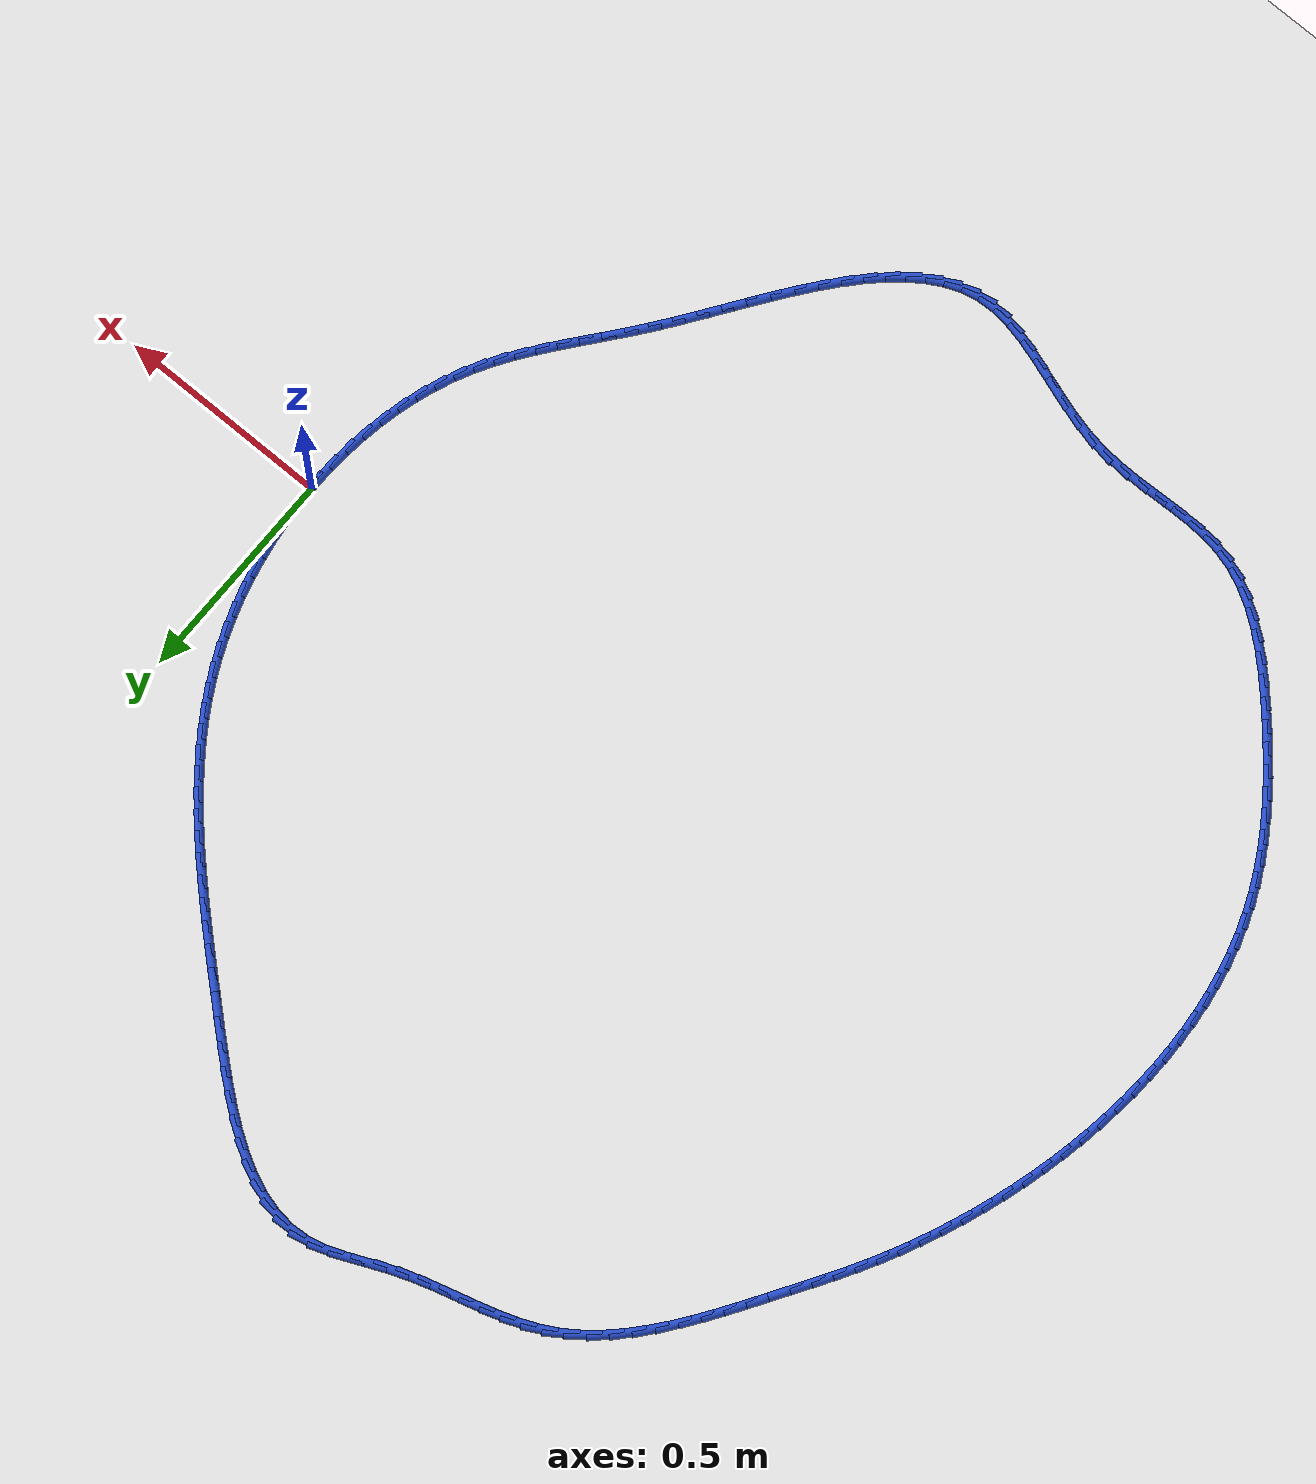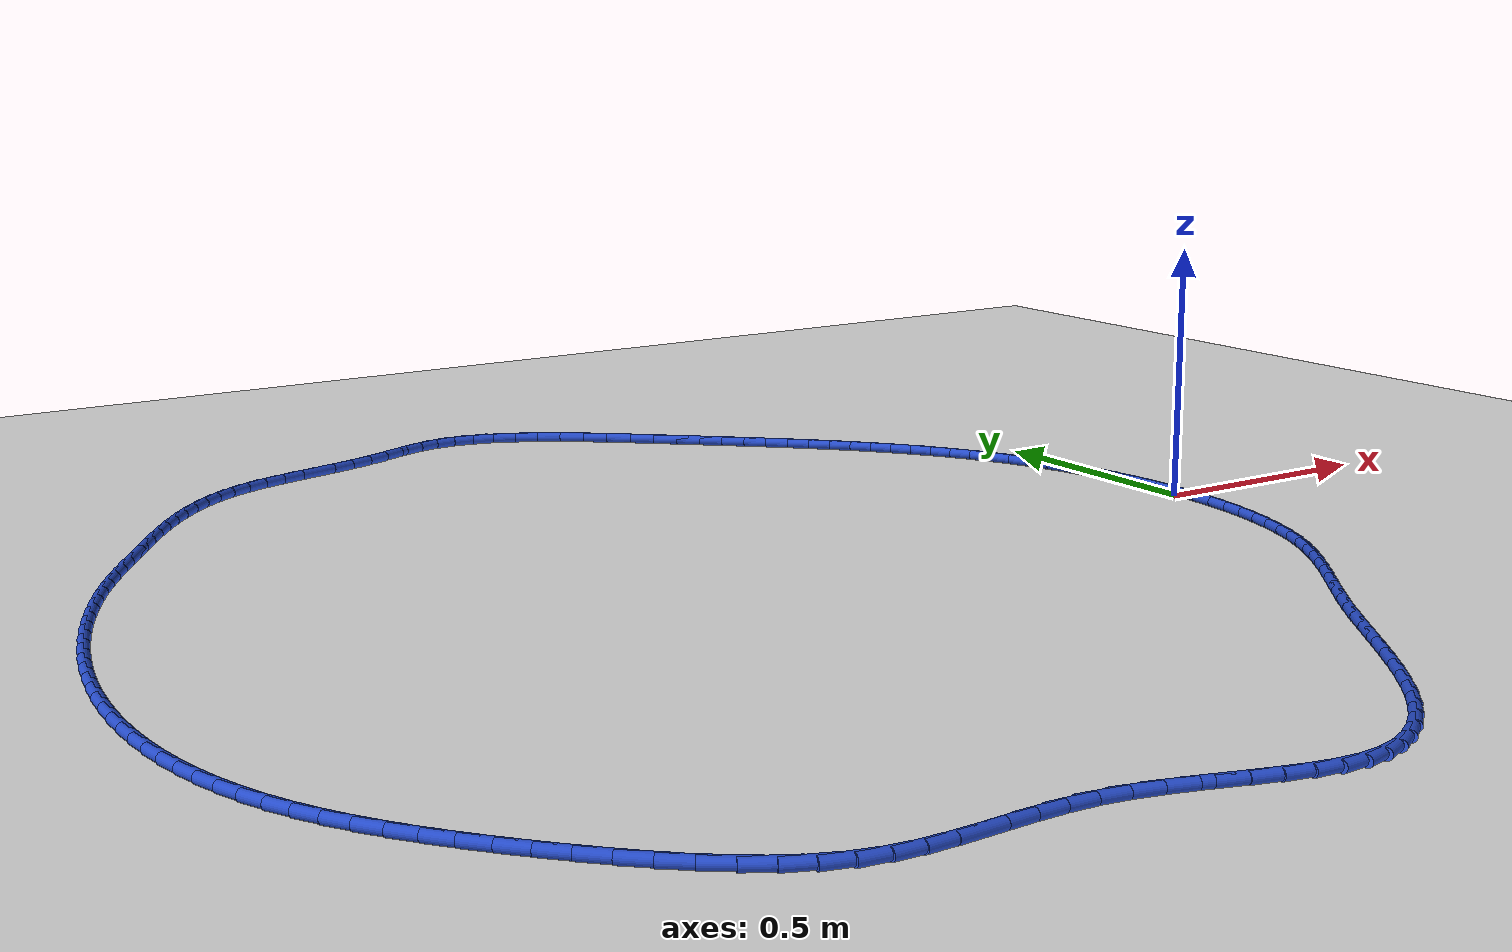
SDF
<sdf version="1.6">
 <world name="default">
  <light name="sun" type="directional">
   <pose>0 0 10 0 -0 0</pose>
   <diffuse>0.8 0.8 0.8 1</diffuse>
   <specular>0.2 0.2 0.2 1</specular>
   <attenuation>
    <range>1000</range>
    <constant>0.9</constant>
    <linear>0.01</linear>
    <quadratic>0.001</quadratic>
   </attenuation>
   <direction>-0.5 0.1 -0.9</direction>
  </light>
  <model name="ground_plane">
   <static>1</static>
   <link name="link">
    <collision name="collision">
     <geometry><plane><normal>0 0 1</normal><size>100 100</size></plane></geometry>
     <surface><friction><ode><mu>100</mu><mu2>50</mu2></ode></friction></surface>
    </collision>
    <visual name="visual">
     <cast_shadows>0</cast_shadows>
     <geometry><plane><normal>0 0 1</normal><size>100 100</size></plane></geometry>
     <material>
      <script><uri>file://media/materials/scripts/gazebo.material</uri><name>Gazebo/WhiteGlow</name></script>
     </material>
    </visual>
   </link>
  </model>
  <gravity>0 0 -9.8</gravity>
  <magnetic_field>6e-06 2.3e-05 -4.2e-05</magnetic_field>
  <atmosphere type="adiabatic"/>
  <physics name="default_physics" default="0" type="ode">
   <max_step_size>0.001</max_step_size>
   <real_time_factor>1</real_time_factor>
   <real_time_update_rate>1000</real_time_update_rate>
  </physics>
  <scene><ambient>0.4 0.4 0.4 1</ambient><background>0.7 0.7 0.7 1</background><shadows>1</shadows></scene>
  <spherical_coordinates>
   <surface_model>EARTH_WGS84</surface_model>
   <latitude_deg>0</latitude_deg>
   <longitude_deg>0</longitude_deg>
   <elevation>0</elevation>
   <heading_deg>0</heading_deg>
  </spherical_coordinates>
  <model name="line">
   <link name="link_0">
    <pose>1.214306433183765e-17 -1.3877787807814457e-17 0.01 0 1.57 -1.537332562540502</pose>
    <collision name="collision">
     <geometry><cylinder><radius>0.01</radius><length>0.08</length></cylinder></geometry>
    </collision>
    <visual name="visual">
     <material>
      <script><name>Gazebo/Blue</name><uri>file://media/materials/scripts/gazebo.material</uri></script>
     </material>
     <geometry><cylinder><radius>0.01</radius><length>0.08</length></cylinder></geometry>
    </visual>
   </link>
   <link name="link_1">
    <pose>-0.0016422306877398084 0.04905657434838483 0.01 0 1.57 -1.4911456338027516</pose>
    <collision name="collision">
     <geometry><cylinder><radius>0.01</radius><length>0.08</length></cylinder></geometry>
    </collision>
    <visual name="visual">
     <material>
      <script><name>Gazebo/Blue</name><uri>file://media/materials/scripts/gazebo.material</uri></script>
     </material>
     <geometry><cylinder><radius>0.01</radius><length>0.08</length></cylinder></geometry>
    </visual>
   </link>
   <link name="link_2">
    <pose>-0.005535999918573262 0.09783871639620474 0.01 0 1.57 -1.445310106959644</pose>
    <collision name="collision">
     <geometry><cylinder><radius>0.01</radius><length>0.08</length></cylinder></geometry>
    </collision>
    <visual name="visual">
     <material>
      <script><name>Gazebo/Blue</name><uri>file://media/materials/scripts/gazebo.material</uri></script>
     </material>
     <geometry><cylinder><radius>0.01</radius><length>0.08</length></cylinder></geometry>
    </visual>
   </link>
   <link name="link_3">
    <pose>-0.011636482450962628 0.14619803318886382 0.01 0 1.57 -1.3995928769485018</pose>
    <collision name="collision">
     <geometry><cylinder><radius>0.01</radius><length>0.08</length></cylinder></geometry>
    </collision>
    <visual name="visual">
     <material>
      <script><name>Gazebo/Blue</name><uri>file://media/materials/scripts/gazebo.material</uri></script>
     </material>
     <geometry><cylinder><radius>0.01</radius><length>0.08</length></cylinder></geometry>
    </visual>
   </link>
   <link name="link_4">
    <pose>-0.01989885304337018 0.19398613177176616 0.01 0 1.57 -1.3537522992703988</pose>
    <collision name="collision">
     <geometry><cylinder><radius>0.01</radius><length>0.08</length></cylinder></geometry>
    </collision>
    <visual name="visual">
     <material>
      <script><name>Gazebo/Blue</name><uri>file://media/materials/scripts/gazebo.material</uri></script>
     </material>
     <geometry><cylinder><radius>0.01</radius><length>0.08</length></cylinder></geometry>
    </visual>
   </link>
   <link name="link_5">
    <pose>-0.030278286454258174 0.2410546191903157 0.01 0 1.57 -1.307537648069753</pose>
    <collision name="collision">
     <geometry><cylinder><radius>0.01</radius><length>0.08</length></cylinder></geometry>
    </collision>
    <visual name="visual">
     <material>
      <script><name>Gazebo/Blue</name><uri>file://media/materials/scripts/gazebo.material</uri></script>
     </material>
     <geometry><cylinder><radius>0.01</radius><length>0.08</length></cylinder></geometry>
    </visual>
   </link>
   <link name="link_6">
    <pose>-0.042729957442088906 0.28725510248991665 0.01 0 1.57 -1.2606883885619955</pose>
    <collision name="collision">
     <geometry><cylinder><radius>0.01</radius><length>0.08</length></cylinder></geometry>
    </collision>
    <visual name="visual">
     <material>
      <script><name>Gazebo/Blue</name><uri>file://media/materials/scripts/gazebo.material</uri></script>
     </material>
     <geometry><cylinder><radius>0.01</radius><length>0.08</length></cylinder></geometry>
    </visual>
   </link>
   <link name="link_7">
    <pose>-0.05720904076532463 0.3324391887159729 0.01 0 1.57 -1.2129334757176156</pose>
    <collision name="collision">
     <geometry><cylinder><radius>0.01</radius><length>0.08</length></cylinder></geometry>
    </collision>
    <visual name="visual">
     <material>
      <script><name>Gazebo/Blue</name><uri>file://media/materials/scripts/gazebo.material</uri></script>
     </material>
     <geometry><cylinder><radius>0.01</radius><length>0.08</length></cylinder></geometry>
    </visual>
   </link>
   <link name="link_8">
    <pose>-0.07367071118242763 0.37645848491388867 0.01 0 1.57 -1.1640035975350842</pose>
    <collision name="collision">
     <geometry><cylinder><radius>0.01</radius><length>0.08</length></cylinder></geometry>
    </collision>
    <visual name="visual">
     <material>
      <script><name>Gazebo/Blue</name><uri>file://media/materials/scripts/gazebo.material</uri></script>
     </material>
     <geometry><cylinder><radius>0.01</radius><length>0.08</length></cylinder></geometry>
    </visual>
   </link>
   <link name="link_9">
    <pose>-0.09207000188835714 0.4191657574125525 0.01 0 1.57 -1.1147331889079957</pose>
    <collision name="collision">
     <geometry><cylinder><radius>0.01</radius><length>0.08</length></cylinder></geometry>
    </collision>
    <visual name="visual">
     <material>
      <script><name>Gazebo/Blue</name><uri>file://media/materials/scripts/gazebo.material</uri></script>
     </material>
     <geometry><cylinder><radius>0.01</radius><length>0.08</length></cylinder></geometry>
    </visual>
   </link>
   <link name="link_10">
    <pose>-0.11235048113957313 0.4605076605386113 0.01 0 1.57 -1.0672085268057987</pose>
    <collision name="collision">
     <geometry><cylinder><radius>0.01</radius><length>0.08</length></cylinder></geometry>
    </collision>
    <visual name="visual">
     <material>
      <script><name>Gazebo/Blue</name><uri>file://media/materials/scripts/gazebo.material</uri></script>
     </material>
     <geometry><cylinder><radius>0.01</radius><length>0.08</length></cylinder></geometry>
    </visual>
   </link>
   <link name="link_11">
    <pose>-0.13443598775151117 0.5005924157928237 0.01 0 1.57 -1.0220870463493974</pose>
    <collision name="collision">
     <geometry><cylinder><radius>0.01</radius><length>0.08</length></cylinder></geometry>
    </collision>
    <visual name="visual">
     <material>
      <script><name>Gazebo/Blue</name><uri>file://media/materials/scripts/gazebo.material</uri></script>
     </material>
     <geometry><cylinder><radius>0.01</radius><length>0.08</length></cylinder></geometry>
    </visual>
   </link>
   <link name="link_12">
    <pose>-0.15824841181752827 0.5395442030357892 0.01 0 1.57 -0.9797728386964492</pose>
    <collision name="collision">
     <geometry><cylinder><radius>0.01</radius><length>0.08</length></cylinder></geometry>
    </collision>
    <visual name="visual">
     <material>
      <script><name>Gazebo/Blue</name><uri>file://media/materials/scripts/gazebo.material</uri></script>
     </material>
     <geometry><cylinder><radius>0.01</radius><length>0.08</length></cylinder></geometry>
    </visual>
   </link>
   <link name="link_13">
    <pose>-0.18370964343098145 0.5774872021281077 0.01 0 1.57 -0.9405829895709513</pose>
    <collision name="collision">
     <geometry><cylinder><radius>0.01</radius><length>0.08</length></cylinder></geometry>
    </collision>
    <visual name="visual">
     <material>
      <script><name>Gazebo/Blue</name><uri>file://media/materials/scripts/gazebo.material</uri></script>
     </material>
     <geometry><cylinder><radius>0.01</radius><length>0.08</length></cylinder></geometry>
    </visual>
   </link>
   <link name="link_14">
    <pose>-0.21074157268522775 0.6145455929303787 0.01 0 1.57 -0.9047472154058953</pose>
    <collision name="collision">
     <geometry><cylinder><radius>0.01</radius><length>0.08</length></cylinder></geometry>
    </collision>
    <visual name="visual">
     <material>
      <script><name>Gazebo/Blue</name><uri>file://media/materials/scripts/gazebo.material</uri></script>
     </material>
     <geometry><cylinder><radius>0.01</radius><length>0.08</length></cylinder></geometry>
    </visual>
   </link>
   <link name="link_15">
    <pose>-0.23926608967362428 0.6508435553032024 0.01 0 1.57 -0.8724135066609254</pose>
    <collision name="collision">
     <geometry><cylinder><radius>0.01</radius><length>0.08</length></cylinder></geometry>
    </collision>
    <visual name="visual">
     <material>
      <script><name>Gazebo/Blue</name><uri>file://media/materials/scripts/gazebo.material</uri></script>
     </material>
     <geometry><cylinder><radius>0.01</radius><length>0.08</length></cylinder></geometry>
    </visual>
   </link>
   <link name="link_16">
    <pose>-0.26920508448952807 0.6865052691071781 0.01 0 1.57 -0.8436578181014758</pose>
    <collision name="collision">
     <geometry><cylinder><radius>0.01</radius><length>0.08</length></cylinder></geometry>
    </collision>
    <visual name="visual">
     <material>
      <script><name>Gazebo/Blue</name><uri>file://media/materials/scripts/gazebo.material</uri></script>
     </material>
     <geometry><cylinder><radius>0.01</radius><length>0.08</length></cylinder></geometry>
    </visual>
   </link>
   <link name="link_17">
    <pose>-0.3004804472262961 0.7216549142029057 0.01 0 1.57 -0.8184958578874907</pose>
    <collision name="collision">
     <geometry><cylinder><radius>0.01</radius><length>0.08</length></cylinder></geometry>
    </collision>
    <visual name="visual">
     <material>
      <script><name>Gazebo/Blue</name><uri>file://media/materials/scripts/gazebo.material</uri></script>
     </material>
     <geometry><cylinder><radius>0.01</radius><length>0.08</length></cylinder></geometry>
    </visual>
   </link>
   <link name="link_18">
    <pose>-0.33301406797728544 0.7564166704509854 0.01 0 1.57 -0.7968953480509642</pose>
    <collision name="collision">
     <geometry><cylinder><radius>0.01</radius><length>0.08</length></cylinder></geometry>
    </collision>
    <visual name="visual">
     <material>
      <script><name>Gazebo/Blue</name><uri>file://media/materials/scripts/gazebo.material</uri></script>
     </material>
     <geometry><cylinder><radius>0.01</radius><length>0.08</length></cylinder></geometry>
    </visual>
   </link>
   <link name="link_19">
    <pose>-0.36672783683585325 0.7909147177120166 0.01 0 1.57 -0.7787875855207196</pose>
    <collision name="collision">
     <geometry><cylinder><radius>0.01</radius><length>0.08</length></cylinder></geometry>
    </collision>
    <visual name="visual">
     <material>
      <script><name>Gazebo/Blue</name><uri>file://media/materials/scripts/gazebo.material</uri></script>
     </material>
     <geometry><cylinder><radius>0.01</radius><length>0.08</length></cylinder></geometry>
    </visual>
   </link>
   <link name="link_20">
    <pose>-0.40154364389535635 0.825273235846599 0.01 0 1.57 -0.7640775906510089</pose>
    <collision name="collision">
     <geometry><cylinder><radius>0.01</radius><length>0.08</length></cylinder></geometry>
    </collision>
    <visual name="visual">
     <material>
      <script><name>Gazebo/Blue</name><uri>file://media/materials/scripts/gazebo.material</uri></script>
     </material>
     <geometry><cylinder><radius>0.01</radius><length>0.08</length></cylinder></geometry>
    </visual>
   </link>
   <link name="link_21">
    <pose>-0.4373833792491522 0.8596164047153326 0.01 0 1.57 -0.7526525111310162</pose>
    <collision name="collision">
     <geometry><cylinder><radius>0.01</radius><length>0.08</length></cylinder></geometry>
    </collision>
    <visual name="visual">
     <material>
      <script><name>Gazebo/Blue</name><uri>file://media/materials/scripts/gazebo.material</uri></script>
     </material>
     <geometry><cylinder><radius>0.01</radius><length>0.08</length></cylinder></geometry>
    </visual>
   </link>
   <link name="link_22">
    <pose>-0.47416893299059726 0.8940684041788167 0.01 0 1.57 -0.744388224784669</pose>
    <collision name="collision">
     <geometry><cylinder><radius>0.01</radius><length>0.08</length></cylinder></geometry>
    </collision>
    <visual name="visual">
     <material>
      <script><name>Gazebo/Blue</name><uri>file://media/materials/scripts/gazebo.material</uri></script>
     </material>
     <geometry><cylinder><radius>0.01</radius><length>0.08</length></cylinder></geometry>
    </visual>
   </link>
   <link name="link_23">
    <pose>-0.5118221952130491 0.9287534140976517 0.01 0 1.57 -0.7391542593172409</pose>
    <collision name="collision">
     <geometry><cylinder><radius>0.01</radius><length>0.08</length></cylinder></geometry>
    </collision>
    <visual name="visual">
     <material>
      <script><name>Gazebo/Blue</name><uri>file://media/materials/scripts/gazebo.material</uri></script>
     </material>
     <geometry><cylinder><radius>0.01</radius><length>0.08</length></cylinder></geometry>
    </visual>
   </link>
   <link name="link_24">
    <pose>-0.5502650560098644 0.9637956143324369 0.01 0 1.57 -0.7368172405692104</pose>
    <collision name="collision">
     <geometry><cylinder><radius>0.01</radius><length>0.08</length></cylinder></geometry>
    </collision>
    <visual name="visual">
     <material>
      <script><name>Gazebo/Blue</name><uri>file://media/materials/scripts/gazebo.material</uri></script>
     </material>
     <geometry><cylinder><radius>0.01</radius><length>0.08</length></cylinder></geometry>
    </visual>
   </link>
   <link name="link_25">
    <pose>-0.5894194054744006 0.9993191847437723 0.01 0 1.57 -0.7360771575367355</pose>
    <collision name="collision">
     <geometry><cylinder><radius>0.01</radius><length>0.08</length></cylinder></geometry>
    </collision>
    <visual name="visual">
     <material>
      <script><name>Gazebo/Blue</name><uri>file://media/materials/scripts/gazebo.material</uri></script>
     </material>
     <geometry><cylinder><radius>0.01</radius><length>0.08</length></cylinder></geometry>
    </visual>
   </link>
   <link name="link_26">
    <pose>-0.6292101267349934 1.0353664636753468 0.01 0 1.57 -0.7282410911223244</pose>
    <collision name="collision">
     <geometry><cylinder><radius>0.01</radius><length>0.08</length></cylinder></geometry>
    </collision>
    <visual name="visual">
     <material>
      <script><name>Gazebo/Blue</name><uri>file://media/materials/scripts/gazebo.material</uri></script>
     </material>
     <geometry><cylinder><radius>0.01</radius><length>0.08</length></cylinder></geometry>
    </visual>
   </link>
   <link name="link_27">
    <pose>-0.6695843885835848 1.0713704105201638 0.01 0 1.57 -0.709311309106551</pose>
    <collision name="collision">
     <geometry><cylinder><radius>0.01</radius><length>0.08</length></cylinder></geometry>
    </collision>
    <visual name="visual">
     <material>
      <script><name>Gazebo/Blue</name><uri>file://media/materials/scripts/gazebo.material</uri></script>
     </material>
     <geometry><cylinder><radius>0.01</radius><length>0.08</length></cylinder></geometry>
    </visual>
   </link>
   <link name="link_28">
    <pose>-0.7104994133495276 1.1064890808502457 0.01 0 1.57 -0.6785525414129072</pose>
    <collision name="collision">
     <geometry><cylinder><radius>0.01</radius><length>0.08</length></cylinder></geometry>
    </collision>
    <visual name="visual">
     <material>
      <script><name>Gazebo/Blue</name><uri>file://media/materials/scripts/gazebo.material</uri></script>
     </material>
     <geometry><cylinder><radius>0.01</radius><length>0.08</length></cylinder></geometry>
    </visual>
   </link>
   <link name="link_29">
    <pose>-0.7519124721950791 1.13987919495119 0.01 0 1.57 -0.6345297226421365</pose>
    <collision name="collision">
     <geometry><cylinder><radius>0.01</radius><length>0.08</length></cylinder></geometry>
    </collision>
    <visual name="visual">
     <material>
      <script><name>Gazebo/Blue</name><uri>file://media/materials/scripts/gazebo.material</uri></script>
     </material>
     <geometry><cylinder><radius>0.01</radius><length>0.08</length></cylinder></geometry>
    </visual>
   </link>
   <link name="link_30">
    <pose>-0.7937808362824971 1.1706974731085955 0.01 0 1.57 -0.5750531235269352</pose>
    <collision name="collision">
     <geometry><cylinder><radius>0.01</radius><length>0.08</length></cylinder></geometry>
    </collision>
    <visual name="visual">
     <material>
      <script><name>Gazebo/Blue</name><uri>file://media/materials/scripts/gazebo.material</uri></script>
     </material>
     <geometry><cylinder><radius>0.01</radius><length>0.08</length></cylinder></geometry>
    </visual>
   </link>
   <link name="link_31">
    <pose>-0.8360617767740391 1.1981006356080601 0.01 0 1.57 -0.49718845021217367</pose>
    <collision name="collision">
     <geometry><cylinder><radius>0.01</radius><length>0.08</length></cylinder></geometry>
    </collision>
    <visual name="visual">
     <material>
      <script><name>Gazebo/Blue</name><uri>file://media/materials/scripts/gazebo.material</uri></script>
     </material>
     <geometry><cylinder><radius>0.01</radius><length>0.08</length></cylinder></geometry>
    </visual>
   </link>
   <link name="link_32">
    <pose>-0.8787125648319619 1.2212454027351807 0.01 0 1.57 -0.3974770933280242</pose>
    <collision name="collision">
     <geometry><cylinder><radius>0.01</radius><length>0.08</length></cylinder></geometry>
    </collision>
    <visual name="visual">
     <material>
      <script><name>Gazebo/Blue</name><uri>file://media/materials/scripts/gazebo.material</uri></script>
     </material>
     <geometry><cylinder><radius>0.01</radius><length>0.08</length></cylinder></geometry>
    </visual>
   </link>
   <link name="link_33">
    <pose>-0.9216904716185235 1.239288494775556 0.01 0 1.57 -0.27268060225712776</pose>
    <collision name="collision">
     <geometry><cylinder><radius>0.01</radius><length>0.08</length></cylinder></geometry>
    </collision>
    <visual name="visual">
     <material>
      <script><name>Gazebo/Blue</name><uri>file://media/materials/scripts/gazebo.material</uri></script>
     </material>
     <geometry><cylinder><radius>0.01</radius><length>0.08</length></cylinder></geometry>
    </visual>
   </link>
   <link name="link_34">
    <pose>-0.964952768295981 1.2513866320147833 0.01 0 1.57 -0.12145487417875042</pose>
    <collision name="collision">
     <geometry><cylinder><radius>0.01</radius><length>0.08</length></cylinder></geometry>
    </collision>
    <visual name="visual">
     <material>
      <script><name>Gazebo/Blue</name><uri>file://media/materials/scripts/gazebo.material</uri></script>
     </material>
     <geometry><cylinder><radius>0.01</radius><length>0.08</length></cylinder></geometry>
    </visual>
   </link>
   <link name="link_35">
    <pose>-1.008456726026592 1.2566965347384613 0.01 0 1.57 0.05307272191786943</pose>
    <collision name="collision">
     <geometry><cylinder><radius>0.01</radius><length>0.08</length></cylinder></geometry>
    </collision>
    <visual name="visual">
     <material>
      <script><name>Gazebo/Blue</name><uri>file://media/materials/scripts/gazebo.material</uri></script>
     </material>
     <geometry><cylinder><radius>0.01</radius><length>0.08</length></cylinder></geometry>
    </visual>
   </link>
   <link name="link_36">
    <pose>-1.0521596159726143 1.2543749232321877 0.01 0 1.57 0.23320302473969673</pose>
    <collision name="collision">
     <geometry><cylinder><radius>0.01</radius><length>0.08</length></cylinder></geometry>
    </collision>
    <visual name="visual">
     <material>
      <script><name>Gazebo/Blue</name><uri>file://media/materials/scripts/gazebo.material</uri></script>
     </material>
     <geometry><cylinder><radius>0.01</radius><length>0.08</length></cylinder></geometry>
    </visual>
   </link>
   <link name="link_37">
    <pose>-1.096042533343938 1.2439516537236917 0.01 0 1.57 0.35729503241830946</pose>
    <collision name="collision">
     <geometry><cylinder><radius>0.01</radius><length>0.08</length></cylinder></geometry>
    </collision>
    <visual name="visual">
     <material>
      <script><name>Gazebo/Blue</name><uri>file://media/materials/scripts/gazebo.material</uri></script>
     </material>
     <geometry><cylinder><radius>0.01</radius><length>0.08</length></cylinder></geometry>
    </visual>
   </link>
   <link name="link_38">
    <pose>-1.1402457609196315 1.2274498029259584 0.01 0 1.57 0.4117840924104204</pose>
    <collision name="collision">
     <geometry><cylinder><radius>0.01</radius><length>0.08</length></cylinder></geometry>
    </collision>
    <visual name="visual">
     <material>
      <script><name>Gazebo/Blue</name><uri>file://media/materials/scripts/gazebo.material</uri></script>
     </material>
     <geometry><cylinder><radius>0.01</radius><length>0.08</length></cylinder></geometry>
    </visual>
   </link>
   <link name="link_39">
    <pose>-1.1849748190969605 1.207914209282112 0.01 0 1.57 0.40560315037573574</pose>
    <collision name="collision">
     <geometry><cylinder><radius>0.01</radius><length>0.08</length></cylinder></geometry>
    </collision>
    <visual name="visual">
     <material>
      <script><name>Gazebo/Blue</name><uri>file://media/materials/scripts/gazebo.material</uri></script>
     </material>
     <geometry><cylinder><radius>0.01</radius><length>0.08</length></cylinder></geometry>
    </visual>
   </link>
   <link name="link_40">
    <pose>-1.2304354255915213 1.1883928016656802 0.01 0 1.57 0.3495222712939641</pose>
    <collision name="collision">
     <geometry><cylinder><radius>0.01</radius><length>0.08</length></cylinder></geometry>
    </collision>
    <visual name="visual">
     <material>
      <script><name>Gazebo/Blue</name><uri>file://media/materials/scripts/gazebo.material</uri></script>
     </material>
     <geometry><cylinder><radius>0.01</radius><length>0.08</length></cylinder></geometry>
    </visual>
   </link>
   <link name="link_41">
    <pose>-1.2767633190631458 1.1715068772545918 0.01 0 1.57 0.296279965969792</pose>
    <collision name="collision">
     <geometry><cylinder><radius>0.01</radius><length>0.08</length></cylinder></geometry>
    </collision>
    <visual name="visual">
     <material>
      <script><name>Gazebo/Blue</name><uri>file://media/materials/scripts/gazebo.material</uri></script>
     </material>
     <geometry><cylinder><radius>0.01</radius><length>0.08</length></cylinder></geometry>
    </visual>
   </link>
   <link name="link_42">
    <pose>-1.3236538443944248 1.1571928449861273 0.01 0 1.57 0.2669550776240468</pose>
    <collision name="collision">
     <geometry><cylinder><radius>0.01</radius><length>0.08</length></cylinder></geometry>
    </collision>
    <visual name="visual">
     <material>
      <script><name>Gazebo/Blue</name><uri>file://media/materials/scripts/gazebo.material</uri></script>
     </material>
     <geometry><cylinder><radius>0.01</radius><length>0.08</length></cylinder></geometry>
    </visual>
   </link>
   <link name="link_43">
    <pose>-1.3706314575388139 1.1443452787399304 0.01 0 1.57 0.26190749248499134</pose>
    <collision name="collision">
     <geometry><cylinder><radius>0.01</radius><length>0.08</length></cylinder></geometry>
    </collision>
    <visual name="visual">
     <material>
      <script><name>Gazebo/Blue</name><uri>file://media/materials/scripts/gazebo.material</uri></script>
     </material>
     <geometry><cylinder><radius>0.01</radius><length>0.08</length></cylinder></geometry>
    </visual>
   </link>
   <link name="link_44">
    <pose>-1.417220237539508 1.13185645453863 0.01 0 1.57 0.28181028640822947</pose>
    <collision name="collision">
     <geometry><cylinder><radius>0.01</radius><length>0.08</length></cylinder></geometry>
    </collision>
    <visual name="visual">
     <material>
      <script><name>Gazebo/Blue</name><uri>file://media/materials/scripts/gazebo.material</uri></script>
     </material>
     <geometry><cylinder><radius>0.01</radius><length>0.08</length></cylinder></geometry>
    </visual>
   </link>
   <link name="link_45">
    <pose>-1.4629442634397 1.118618648404854 0.01 0 1.57 0.3278227785399708</pose>
    <collision name="collision">
     <geometry><cylinder><radius>0.01</radius><length>0.08</length></cylinder></geometry>
    </collision>
    <visual name="visual">
     <material>
      <script><name>Gazebo/Blue</name><uri>file://media/materials/scripts/gazebo.material</uri></script>
     </material>
     <geometry><cylinder><radius>0.01</radius><length>0.08</length></cylinder></geometry>
    </visual>
   </link>
   <link name="link_46">
    <pose>-1.5073276142825824 1.10352413636123 0.01 0 1.57 0.4012351434614374</pose>
    <collision name="collision">
     <geometry><cylinder><radius>0.01</radius><length>0.08</length></cylinder></geometry>
    </collision>
    <visual name="visual">
     <material>
      <script><name>Gazebo/Blue</name><uri>file://media/materials/scripts/gazebo.material</uri></script>
     </material>
     <geometry><cylinder><radius>0.01</radius><length>0.08</length></cylinder></geometry>
    </visual>
   </link>
   <link name="link_47">
    <pose>-1.5498943691113505 1.0854651944303875 0.01 0 1.57 0.5013650158760009</pose>
    <collision name="collision">
     <geometry><cylinder><radius>0.01</radius><length>0.08</length></cylinder></geometry>
    </collision>
    <visual name="visual">
     <material>
      <script><name>Gazebo/Blue</name><uri>file://media/materials/scripts/gazebo.material</uri></script>
     </material>
     <geometry><cylinder><radius>0.01</radius><length>0.08</length></cylinder></geometry>
    </visual>
   </link>
   <link name="link_48">
    <pose>-1.5901883695828827 1.0633810112213105 0.01 0 1.57 0.6070179470870465</pose>
    <collision name="collision">
     <geometry><cylinder><radius>0.01</radius><length>0.08</length></cylinder></geometry>
    </collision>
    <visual name="visual">
     <material>
      <script><name>Gazebo/Blue</name><uri>file://media/materials/scripts/gazebo.material</uri></script>
     </material>
     <geometry><cylinder><radius>0.01</radius><length>0.08</length></cylinder></geometry>
    </visual>
   </link>
   <link name="link_49">
    <pose>-1.628105993035103 1.037047626219275 0.01 0 1.57 0.6996886548832334</pose>
    <collision name="collision">
     <geometry><cylinder><radius>0.01</radius><length>0.08</length></cylinder></geometry>
    </collision>
    <visual name="visual">
     <material>
      <script><name>Gazebo/Blue</name><uri>file://media/materials/scripts/gazebo.material</uri></script>
     </material>
     <geometry><cylinder><radius>0.01</radius><length>0.08</length></cylinder></geometry>
    </visual>
   </link>
   <link name="link_50">
    <pose>-1.6638473599296186 1.006962105781128 0.01 0 1.57 0.7785693957356142</pose>
    <collision name="collision">
     <geometry><cylinder><radius>0.01</radius><length>0.08</length></cylinder></geometry>
    </collision>
    <visual name="visual">
     <material>
      <script><name>Gazebo/Blue</name><uri>file://media/materials/scripts/gazebo.material</uri></script>
     </material>
     <geometry><cylinder><radius>0.01</radius><length>0.08</length></cylinder></geometry>
    </visual>
   </link>
   <link name="link_51">
    <pose>-1.697622526893216 0.973645102779882 0.01 0 1.57 0.8442426290446318</pose>
    <collision name="collision">
     <geometry><cylinder><radius>0.01</radius><length>0.08</length></cylinder></geometry>
    </collision>
    <visual name="visual">
     <material>
      <script><name>Gazebo/Blue</name><uri>file://media/materials/scripts/gazebo.material</uri></script>
     </material>
     <geometry><cylinder><radius>0.01</radius><length>0.08</length></cylinder></geometry>
    </visual>
   </link>
   <link name="link_52">
    <pose>-1.7296415505526856 0.9376172700885501 0.01 0 1.57 0.8976764139280748</pose>
    <collision name="collision">
     <geometry><cylinder><radius>0.01</radius><length>0.08</length></cylinder></geometry>
    </collision>
    <visual name="visual">
     <material>
      <script><name>Gazebo/Blue</name><uri>file://media/materials/scripts/gazebo.material</uri></script>
     </material>
     <geometry><cylinder><radius>0.01</radius><length>0.08</length></cylinder></geometry>
    </visual>
   </link>
   <link name="link_53">
    <pose>-1.760114487534815 0.8993992605801443 0.01 0 1.57 0.9399077733852775</pose>
    <collision name="collision">
     <geometry><cylinder><radius>0.01</radius><length>0.08</length></cylinder></geometry>
    </collision>
    <visual name="visual">
     <material>
      <script><name>Gazebo/Blue</name><uri>file://media/materials/scripts/gazebo.material</uri></script>
     </material>
     <geometry><cylinder><radius>0.01</radius><length>0.08</length></cylinder></geometry>
    </visual>
   </link>
   <link name="link_54">
    <pose>-1.7892513944663937 0.8595117271276772 0.01 0 1.57 0.9718524993182758</pose>
    <collision name="collision">
     <geometry><cylinder><radius>0.01</radius><length>0.08</length></cylinder></geometry>
    </collision>
    <visual name="visual">
     <material>
      <script><name>Gazebo/Blue</name><uri>file://media/materials/scripts/gazebo.material</uri></script>
     </material>
     <geometry><cylinder><radius>0.01</radius><length>0.08</length></cylinder></geometry>
    </visual>
   </link>
   <link name="link_55">
    <pose>-1.8172623279742086 0.8184753226041613 0.01 0 1.57 0.9942015931221642</pose>
    <collision name="collision">
     <geometry><cylinder><radius>0.01</radius><length>0.08</length></cylinder></geometry>
    </collision>
    <visual name="visual">
     <material>
      <script><name>Gazebo/Blue</name><uri>file://media/materials/scripts/gazebo.material</uri></script>
     </material>
     <geometry><cylinder><radius>0.01</radius><length>0.08</length></cylinder></geometry>
    </visual>
   </link>
   <link name="link_56">
    <pose>-1.8443573446850496 0.7768106998826098 0.01 0 1.57 1.0073650396837266</pose>
    <collision name="collision">
     <geometry><cylinder><radius>0.01</radius><length>0.08</length></cylinder></geometry>
    </collision>
    <visual name="visual">
     <material>
      <script><name>Gazebo/Blue</name><uri>file://media/materials/scripts/gazebo.material</uri></script>
     </material>
     <geometry><cylinder><radius>0.01</radius><length>0.08</length></cylinder></geometry>
    </visual>
   </link>
   <link name="link_57">
    <pose>-1.8707465012257043 0.7350385118360343 0.01 0 1.57 1.011478258368274</pose>
    <collision name="collision">
     <geometry><cylinder><radius>0.01</radius><length>0.08</length></cylinder></geometry>
    </collision>
    <visual name="visual">
     <material>
      <script><name>Gazebo/Blue</name><uri>file://media/materials/scripts/gazebo.material</uri></script>
     </material>
     <geometry><cylinder><radius>0.01</radius><length>0.08</length></cylinder></geometry>
    </visual>
   </link>
   <link name="link_58">
    <pose>-1.8966389118653497 0.6936768312107244 0.01 0 1.57 1.0118130993334504</pose>
    <collision name="collision">
     <geometry><cylinder><radius>0.01</radius><length>0.08</length></cylinder></geometry>
    </collision>
    <visual name="visual">
     <material>
      <script><name>Gazebo/Blue</name><uri>file://media/materials/scripts/gazebo.material</uri></script>
     </material>
     <geometry><cylinder><radius>0.01</radius><length>0.08</length></cylinder></geometry>
    </visual>
   </link>
   <link name="link_59">
    <pose>-1.922128491251638 0.6529283201082964 0.01 0 1.57 1.019064442676933</pose>
    <collision name="collision">
     <geometry><cylinder><radius>0.01</radius><length>0.08</length></cylinder></geometry>
    </collision>
    <visual name="visual">
     <material>
      <script><name>Gazebo/Blue</name><uri>file://media/materials/scripts/gazebo.material</uri></script>
     </material>
     <geometry><cylinder><radius>0.01</radius><length>0.08</length></cylinder></geometry>
    </visual>
   </link>
   <link name="link_60">
    <pose>-1.947084784806442 0.6123813292184679 0.01 0 1.57 1.0345307797100867</pose>
    <collision name="collision">
     <geometry><cylinder><radius>0.01</radius><length>0.08</length></cylinder></geometry>
    </collision>
    <visual name="visual">
     <material>
      <script><name>Gazebo/Blue</name><uri>file://media/materials/scripts/gazebo.material</uri></script>
     </material>
     <geometry><cylinder><radius>0.01</radius><length>0.08</length></cylinder></geometry>
    </visual>
   </link>
   <link name="link_61">
    <pose>-1.9713514705967723 0.5715533857424329 0.01 0 1.57 1.0579392164853803</pose>
    <collision name="collision">
     <geometry><cylinder><radius>0.01</radius><length>0.08</length></cylinder></geometry>
    </collision>
    <visual name="visual">
     <material>
      <script><name>Gazebo/Blue</name><uri>file://media/materials/scripts/gazebo.material</uri></script>
     </material>
     <geometry><cylinder><radius>0.01</radius><length>0.08</length></cylinder></geometry>
    </visual>
   </link>
   <link name="link_62">
    <pose>-1.99477222668964 0.5299620168813848 0.01 0 1.57 1.0875519977489114</pose>
    <collision name="collision">
     <geometry><cylinder><radius>0.01</radius><length>0.08</length></cylinder></geometry>
    </collision>
    <visual name="visual">
     <material>
      <script><name>Gazebo/Blue</name><uri>file://media/materials/scripts/gazebo.material</uri></script>
     </material>
     <geometry><cylinder><radius>0.01</radius><length>0.08</length></cylinder></geometry>
    </visual>
   </link>
   <link name="link_63">
    <pose>-2.0172044860335365 0.4872128544320055 0.01 0 1.57 1.1180129916207924</pose>
    <collision name="collision">
     <geometry><cylinder><radius>0.01</radius><length>0.08</length></cylinder></geometry>
    </collision>
    <visual name="visual">
     <material>
      <script><name>Gazebo/Blue</name><uri>file://media/materials/scripts/gazebo.material</uri></script>
     </material>
     <geometry><cylinder><radius>0.01</radius><length>0.08</length></cylinder></geometry>
    </visual>
   </link>
   <link name="link_64">
    <pose>-2.0385666770933537 0.4433022267815781 0.01 0 1.57 1.1480889474235125</pose>
    <collision name="collision">
     <geometry><cylinder><radius>0.01</radius><length>0.08</length></cylinder></geometry>
    </collision>
    <visual name="visual">
     <material>
      <script><name>Gazebo/Blue</name><uri>file://media/materials/scripts/gazebo.material</uri></script>
     </material>
     <geometry><cylinder><radius>0.01</radius><length>0.08</length></cylinder></geometry>
    </visual>
   </link>
   <link name="link_65">
    <pose>-2.0587941299949777 0.39833472308336537 0.01 0 1.57 1.177958827189347</pose>
    <collision name="collision">
     <geometry><cylinder><radius>0.01</radius><length>0.08</length></cylinder></geometry>
    </collision>
    <visual name="visual">
     <material>
      <script><name>Gazebo/Blue</name><uri>file://media/materials/scripts/gazebo.material</uri></script>
     </material>
     <geometry><cylinder><radius>0.01</radius><length>0.08</length></cylinder></geometry>
    </visual>
   </link>
   <link name="link_66">
    <pose>-2.077822175483266 0.35241493645534117 0.01 0 1.57 1.2077926753106254</pose>
    <collision name="collision">
     <geometry><cylinder><radius>0.01</radius><length>0.08</length></cylinder></geometry>
    </collision>
    <visual name="visual">
     <material>
      <script><name>Gazebo/Blue</name><uri>file://media/materials/scripts/gazebo.material</uri></script>
     </material>
     <geometry><cylinder><radius>0.01</radius><length>0.08</length></cylinder></geometry>
    </visual>
   </link>
   <link name="link_67">
    <pose>-2.0955861443030774 0.30564746001547904 0.01 0 1.57 1.2377539954151593</pose>
    <collision name="collision">
     <geometry><cylinder><radius>0.01</radius><length>0.08</length></cylinder></geometry>
    </collision>
    <visual name="visual">
     <material>
      <script><name>Gazebo/Blue</name><uri>file://media/materials/scripts/gazebo.material</uri></script>
     </material>
     <geometry><cylinder><radius>0.01</radius><length>0.08</length></cylinder></geometry>
    </visual>
   </link>
   <link name="link_68">
    <pose>-2.112021367199268 0.2581368868817535 0.01 0 1.57 1.2680018801175619</pose>
    <collision name="collision">
     <geometry><cylinder><radius>0.01</radius><length>0.08</length></cylinder></geometry>
    </collision>
    <visual name="visual">
     <material>
      <script><name>Gazebo/Blue</name><uri>file://media/materials/scripts/gazebo.material</uri></script>
     </material>
     <geometry><cylinder><radius>0.01</radius><length>0.08</length></cylinder></geometry>
    </visual>
   </link>
   <link name="link_69">
    <pose>-2.1270631749166946 0.2099878101721384 0.01 0 1.57 1.2986928693248518</pose>
    <collision name="collision">
     <geometry><cylinder><radius>0.01</radius><length>0.08</length></cylinder></geometry>
    </collision>
    <visual name="visual">
     <material>
      <script><name>Gazebo/Blue</name><uri>file://media/materials/scripts/gazebo.material</uri></script>
     </material>
     <geometry><cylinder><radius>0.01</radius><length>0.08</length></cylinder></geometry>
    </visual>
   </link>
   <link name="link_70">
    <pose>-2.1406468982002163 0.1613048230046074 0.01 0 1.57 1.329982549413675</pose>
    <collision name="collision">
     <geometry><cylinder><radius>0.01</radius><length>0.08</length></cylinder></geometry>
    </collision>
    <visual name="visual">
     <material>
      <script><name>Gazebo/Blue</name><uri>file://media/materials/scripts/gazebo.material</uri></script>
     </material>
     <geometry><cylinder><radius>0.01</radius><length>0.08</length></cylinder></geometry>
    </visual>
   </link>
   <link name="link_71">
    <pose>-2.152707867794689 0.11219251849713398 0.01 0 1.57 1.3620268903621573</pose>
    <collision name="collision">
     <geometry><cylinder><radius>0.01</radius><length>0.08</length></cylinder></geometry>
    </collision>
    <visual name="visual">
     <material>
      <script><name>Gazebo/Blue</name><uri>file://media/materials/scripts/gazebo.material</uri></script>
     </material>
     <geometry><cylinder><radius>0.01</radius><length>0.08</length></cylinder></geometry>
    </visual>
   </link>
   <link name="link_72">
    <pose>-2.16318141444497 0.06275548976769285 0.01 0 1.57 1.3949833001123526</pose>
    <collision name="collision">
     <geometry><cylinder><radius>0.01</radius><length>0.08</length></cylinder></geometry>
    </collision>
    <visual name="visual">
     <material>
      <script><name>Gazebo/Blue</name><uri>file://media/materials/scripts/gazebo.material</uri></script>
     </material>
     <geometry><cylinder><radius>0.01</radius><length>0.08</length></cylinder></geometry>
    </visual>
   </link>
   <link name="link_73">
    <pose>-2.172002868895918 0.013098329934257656 0.01 0 1.57 1.429011354672205</pose>
    <collision name="collision">
     <geometry><cylinder><radius>0.01</radius><length>0.08</length></cylinder></geometry>
    </collision>
    <visual name="visual">
     <material>
      <script><name>Gazebo/Blue</name><uri>file://media/materials/scripts/gazebo.material</uri></script>
     </material>
     <geometry><cylinder><radius>0.01</radius><length>0.08</length></cylinder></geometry>
    </visual>
   </link>
   <link name="link_74">
    <pose>-2.179107561892389 -0.03667436788519777 0.01 0 1.57 1.4642731383805496</pose>
    <collision name="collision">
     <geometry><cylinder><radius>0.01</radius><length>0.08</length></cylinder></geometry>
    </collision>
    <visual name="visual">
     <material>
      <script><name>Gazebo/Blue</name><uri>file://media/materials/scripts/gazebo.material</uri></script>
     </material>
     <geometry><cylinder><radius>0.01</radius><length>0.08</length></cylinder></geometry>
    </visual>
   </link>
   <link name="link_75">
    <pose>-2.184430824179241 -0.08645801057269958 0.01 0 1.57 1.500933101270726</pose>
    <collision name="collision">
     <geometry><cylinder><radius>0.01</radius><length>0.08</length></cylinder></geometry>
    </collision>
    <visual name="visual">
     <material>
      <script><name>Gazebo/Blue</name><uri>file://media/materials/scripts/gazebo.material</uri></script>
     </material>
     <geometry><cylinder><radius>0.01</radius><length>0.08</length></cylinder></geometry>
    </visual>
   </link>
   <link name="link_76">
    <pose>-2.1879079865013322 -0.13614800501027435 0.01 0 1.57 1.539157310136114</pose>
    <collision name="collision">
     <geometry><cylinder><radius>0.01</radius><length>0.08</length></cylinder></geometry>
    </collision>
    <visual name="visual">
     <material>
      <script><name>Gazebo/Blue</name><uri>file://media/materials/scripts/gazebo.material</uri></script>
     </material>
     <geometry><cylinder><radius>0.01</radius><length>0.08</length></cylinder></geometry>
    </visual>
   </link>
   <link name="link_77">
    <pose>-2.189474379603518 -0.1856397580799476 0.01 0 1.57 -1.5624807151453546</pose>
    <collision name="collision">
     <geometry><cylinder><radius>0.01</radius><length>0.08</length></cylinder></geometry>
    </collision>
    <visual name="visual">
     <material>
      <script><name>Gazebo/Blue</name><uri>file://media/materials/scripts/gazebo.material</uri></script>
     </material>
     <geometry><cylinder><radius>0.01</radius><length>0.08</length></cylinder></geometry>
    </visual>
   </link>
   <link name="link_78">
    <pose>-2.189065334230657 -0.2348286766637447 0.01 0 1.57 -1.5206318423175194</pose>
    <collision name="collision">
     <geometry><cylinder><radius>0.01</radius><length>0.08</length></cylinder></geometry>
    </collision>
    <visual name="visual">
     <material>
      <script><name>Gazebo/Blue</name><uri>file://media/materials/scripts/gazebo.material</uri></script>
     </material>
     <geometry><cylinder><radius>0.01</radius><length>0.08</length></cylinder></geometry>
    </visual>
   </link>
   <link name="link_79">
    <pose>-2.186616181127607 -0.2836101676436934 0.01 0 1.57 -1.476730852269604</pose>
    <collision name="collision">
     <geometry><cylinder><radius>0.01</radius><length>0.08</length></cylinder></geometry>
    </collision>
    <visual name="visual">
     <material>
      <script><name>Gazebo/Blue</name><uri>file://media/materials/scripts/gazebo.material</uri></script>
     </material>
     <geometry><cylinder><radius>0.01</radius><length>0.08</length></cylinder></geometry>
    </visual>
   </link>
   <link name="link_80">
    <pose>-2.182062251039225 -0.33187963790181824 0.01 0 1.57 -1.4306307826380125</pose>
    <collision name="collision">
     <geometry><cylinder><radius>0.01</radius><length>0.08</length></cylinder></geometry>
    </collision>
    <visual name="visual">
     <material>
      <script><name>Gazebo/Blue</name><uri>file://media/materials/scripts/gazebo.material</uri></script>
     </material>
     <geometry><cylinder><radius>0.01</radius><length>0.08</length></cylinder></geometry>
    </visual>
   </link>
   <link name="link_81">
    <pose>-2.1753388747103677 -0.3795324943201468 0.01 0 1.57 -1.3822020659930077</pose>
    <collision name="collision">
     <geometry><cylinder><radius>0.01</radius><length>0.08</length></cylinder></geometry>
    </collision>
    <visual name="visual">
     <material>
      <script><name>Gazebo/Blue</name><uri>file://media/materials/scripts/gazebo.material</uri></script>
     </material>
     <geometry><cylinder><radius>0.01</radius><length>0.08</length></cylinder></geometry>
    </visual>
   </link>
   <link name="link_82">
    <pose>-2.166381382885893 -0.4264641437807044 0.01 0 1.57 -1.3313406291985848</pose>
    <collision name="collision">
     <geometry><cylinder><radius>0.01</radius><length>0.08</length></cylinder></geometry>
    </collision>
    <visual name="visual">
     <material>
      <script><name>Gazebo/Blue</name><uri>file://media/materials/scripts/gazebo.material</uri></script>
     </material>
     <geometry><cylinder><radius>0.01</radius><length>0.08</length></cylinder></geometry>
    </visual>
   </link>
   <link name="link_83">
    <pose>-2.155125106310659 -0.4725699931655164 0.01 0 1.57 -1.2779775386287648</pose>
    <collision name="collision">
     <geometry><cylinder><radius>0.01</radius><length>0.08</length></cylinder></geometry>
    </collision>
    <visual name="visual">
     <material>
      <script><name>Gazebo/Blue</name><uri>file://media/materials/scripts/gazebo.material</uri></script>
     </material>
     <geometry><cylinder><radius>0.01</radius><length>0.08</length></cylinder></geometry>
    </visual>
   </link>
   <link name="link_84">
    <pose>-2.141505375729521 -0.5177454493566105 0.01 0 1.57 -1.2220898764071553</pose>
    <collision name="collision">
     <geometry><cylinder><radius>0.01</radius><length>0.08</length></cylinder></geometry>
    </collision>
    <visual name="visual">
     <material>
      <script><name>Gazebo/Blue</name><uri>file://media/materials/scripts/gazebo.material</uri></script>
     </material>
     <geometry><cylinder><radius>0.01</radius><length>0.08</length></cylinder></geometry>
    </visual>
   </link>
   <link name="link_85">
    <pose>-2.1254575218873386 -0.5618859192360112 0.01 0 1.57 -1.1642877581734437</pose>
    <collision name="collision">
     <geometry><cylinder><radius>0.01</radius><length>0.08</length></cylinder></geometry>
    </collision>
    <visual name="visual">
     <material>
      <script><name>Gazebo/Blue</name><uri>file://media/materials/scripts/gazebo.material</uri></script>
     </material>
     <geometry><cylinder><radius>0.01</radius><length>0.08</length></cylinder></geometry>
    </visual>
   </link>
   <link name="link_86">
    <pose>-2.106937928639904 -0.604906067989191 0.01 0 1.57 -1.108700766443837</pose>
    <collision name="collision">
     <geometry><cylinder><radius>0.01</radius><length>0.08</length></cylinder></geometry>
    </collision>
    <visual name="visual">
     <material>
      <script><name>Gazebo/Blue</name><uri>file://media/materials/scripts/gazebo.material</uri></script>
     </material>
     <geometry><cylinder><radius>0.01</radius><length>0.08</length></cylinder></geometry>
    </visual>
   </link>
   <link name="link_87">
    <pose>-2.086046399784559 -0.6468517539902562 0.01 0 1.57 -1.0573465957903803</pose>
    <collision name="collision">
     <geometry><cylinder><radius>0.01</radius><length>0.08</length></cylinder></geometry>
    </collision>
    <visual name="visual">
     <material>
      <script><name>Gazebo/Blue</name><uri>file://media/materials/scripts/gazebo.material</uri></script>
     </material>
     <geometry><cylinder><radius>0.01</radius><length>0.08</length></cylinder></geometry>
    </visual>
   </link>
   <link name="link_88">
    <pose>-2.062942547039671 -0.6878235448244603 0.01 0 1.57 -1.0105002901631277</pose>
    <collision name="collision">
     <geometry><cylinder><radius>0.01</radius><length>0.08</length></cylinder></geometry>
    </collision>
    <visual name="visual">
     <material>
      <script><name>Gazebo/Blue</name><uri>file://media/materials/scripts/gazebo.material</uri></script>
     </material>
     <geometry><cylinder><radius>0.01</radius><length>0.08</length></cylinder></geometry>
    </visual>
   </link>
   <link name="link_89">
    <pose>-2.0377861806191366 -0.7279221896505657 0.01 0 1.57 -0.9682970698901311</pose>
    <collision name="collision">
     <geometry><cylinder><radius>0.01</radius><length>0.08</length></cylinder></geometry>
    </collision>
    <visual name="visual">
     <material>
      <script><name>Gazebo/Blue</name><uri>file://media/materials/scripts/gazebo.material</uri></script>
     </material>
     <geometry><cylinder><radius>0.01</radius><length>0.08</length></cylinder></geometry>
    </visual>
   </link>
   <link name="link_90">
    <pose>-2.010737110736854 -0.7672484376273323 0.01 0 1.57 -0.9307643834227988</pose>
    <collision name="collision">
     <geometry><cylinder><radius>0.01</radius><length>0.08</length></cylinder></geometry>
    </collision>
    <visual name="visual">
     <material>
      <script><name>Gazebo/Blue</name><uri>file://media/materials/scripts/gazebo.material</uri></script>
     </material>
     <geometry><cylinder><radius>0.01</radius><length>0.08</length></cylinder></geometry>
    </visual>
   </link>
   <link name="link_91">
    <pose>-1.9819551476067234 -0.8059030379135214 0.01 0 1.57 -0.8978498238383492</pose>
    <collision name="collision">
     <geometry><cylinder><radius>0.01</radius><length>0.08</length></cylinder></geometry>
    </collision>
    <visual name="visual">
     <material>
      <script><name>Gazebo/Blue</name><uri>file://media/materials/scripts/gazebo.material</uri></script>
     </material>
     <geometry><cylinder><radius>0.01</radius><length>0.08</length></cylinder></geometry>
    </visual>
   </link>
   <link name="link_92">
    <pose>-1.9516001014426398 -0.8439867396678942 0.01 0 1.57 -0.8694469621531068</pose>
    <collision name="collision">
     <geometry><cylinder><radius>0.01</radius><length>0.08</length></cylinder></geometry>
    </collision>
    <visual name="visual">
     <material>
      <script><name>Gazebo/Blue</name><uri>file://media/materials/scripts/gazebo.material</uri></script>
     </material>
     <geometry><cylinder><radius>0.01</radius><length>0.08</length></cylinder></geometry>
    </visual>
   </link>
   <link name="link_93">
    <pose>-1.919831782458504 -0.8816002920492114 0.01 0 1.57 -0.8454172801910078</pose>
    <collision name="collision">
     <geometry><cylinder><radius>0.01</radius><length>0.08</length></cylinder></geometry>
    </collision>
    <visual name="visual">
     <material>
      <script><name>Gazebo/Blue</name><uri>file://media/materials/scripts/gazebo.material</uri></script>
     </material>
     <geometry><cylinder><radius>0.01</radius><length>0.08</length></cylinder></geometry>
    </visual>
   </link>
   <link name="link_94">
    <pose>-1.8868100008682138 -0.9188444442162355 0.01 0 1.57 -0.8236168186384818</pose>
    <collision name="collision">
     <geometry><cylinder><radius>0.01</radius><length>0.08</length></cylinder></geometry>
    </collision>
    <visual name="visual">
     <material>
      <script><name>Gazebo/Blue</name><uri>file://media/materials/scripts/gazebo.material</uri></script>
     </material>
     <geometry><cylinder><radius>0.01</radius><length>0.08</length></cylinder></geometry>
    </visual>
   </link>
   <link name="link_95">
    <pose>-1.8526653097742622 -0.9557041499098344 0.01 0 1.57 -0.7931818084738356</pose>
    <collision name="collision">
     <geometry><cylinder><radius>0.01</radius><length>0.08</length></cylinder></geometry>
    </collision>
    <visual name="visual">
     <material>
      <script><name>Gazebo/Blue</name><uri>file://media/materials/scripts/gazebo.material</uri></script>
     </material>
     <geometry><cylinder><radius>0.01</radius><length>0.08</length></cylinder></geometry>
    </visual>
   </link>
   <link name="link_96">
    <pose>-1.8173730662089806 -0.9915501192583671 0.01 0 1.57 -0.7497382835807617</pose>
    <collision name="collision">
     <geometry><cylinder><radius>0.01</radius><length>0.08</length></cylinder></geometry>
    </collision>
    <visual name="visual">
     <material>
      <script><name>Gazebo/Blue</name><uri>file://media/materials/scripts/gazebo.material</uri></script>
     </material>
     <geometry><cylinder><radius>0.01</radius><length>0.08</length></cylinder></geometry>
    </visual>
   </link>
   <link name="link_97">
    <pose>-1.7808573643439518 -1.0255501713972945 0.01 0 1.57 -0.6917538439461745</pose>
    <collision name="collision">
     <geometry><cylinder><radius>0.01</radius><length>0.08</length></cylinder></geometry>
    </collision>
    <visual name="visual">
     <material>
      <script><name>Gazebo/Blue</name><uri>file://media/materials/scripts/gazebo.material</uri></script>
     </material>
     <geometry><cylinder><radius>0.01</radius><length>0.08</length></cylinder></geometry>
    </visual>
   </link>
   <link name="link_98">
    <pose>-1.7430422661124725 -1.0568719978675796 0.01 0 1.57 -0.6171697925468734</pose>
    <collision name="collision">
     <geometry><cylinder><radius>0.01</radius><length>0.08</length></cylinder></geometry>
    </collision>
    <visual name="visual">
     <material>
      <script><name>Gazebo/Blue</name><uri>file://media/materials/scripts/gazebo.material</uri></script>
     </material>
     <geometry><cylinder><radius>0.01</radius><length>0.08</length></cylinder></geometry>
    </visual>
   </link>
   <link name="link_99">
    <pose>-1.7038518334478365 -1.084683290210186 0.01 0 1.57 -0.5236716718860327</pose>
    <collision name="collision">
     <geometry><cylinder><radius>0.01</radius><length>0.08</length></cylinder></geometry>
    </collision>
    <visual name="visual">
     <material>
      <script><name>Gazebo/Blue</name><uri>file://media/materials/scripts/gazebo.material</uri></script>
     </material>
     <geometry><cylinder><radius>0.01</radius><length>0.08</length></cylinder></geometry>
    </visual>
   </link>
   <link name="link_100">
    <pose>-1.6632101282833387 -1.108151739966076 0.01 0 1.57 -0.4093090962679287</pose>
    <collision name="collision">
     <geometry><cylinder><radius>0.01</radius><length>0.08</length></cylinder></geometry>
    </collision>
    <visual name="visual">
     <material>
      <script><name>Gazebo/Blue</name><uri>file://media/materials/scripts/gazebo.material</uri></script>
     </material>
     <geometry><cylinder><radius>0.01</radius><length>0.08</length></cylinder></geometry>
    </visual>
   </link>
   <link name="link_101">
    <pose>-1.621041212552274 -1.1264450386762128 0.01 0 1.57 -0.27437590828537956</pose>
    <collision name="collision">
     <geometry><cylinder><radius>0.01</radius><length>0.08</length></cylinder></geometry>
    </collision>
    <visual name="visual">
     <material>
      <script><name>Gazebo/Blue</name><uri>file://media/materials/scripts/gazebo.material</uri></script>
     </material>
     <geometry><cylinder><radius>0.01</radius><length>0.08</length></cylinder></geometry>
    </visual>
   </link>
   <link name="link_102">
    <pose>-1.5772737617688624 -1.138764480119263 0.01 0 1.57 -0.14454596433779343</pose>
    <collision name="collision">
     <geometry><cylinder><radius>0.01</radius><length>0.08</length></cylinder></geometry>
    </collision>
    <visual name="visual">
     <material>
      <script><name>Gazebo/Blue</name><uri>file://media/materials/scripts/gazebo.material</uri></script>
     </material>
     <geometry><cylinder><radius>0.01</radius><length>0.08</length></cylinder></geometry>
    </visual>
   </link>
   <link name="link_103">
    <pose>-1.5319800837361057 -1.1453574795979384 0.01 0 1.57 -0.05017468203903243</pose>
    <collision name="collision">
     <geometry><cylinder><radius>0.01</radius><length>0.08</length></cylinder></geometry>
    </collision>
    <visual name="visual">
     <material>
      <script><name>Gazebo/Blue</name><uri>file://media/materials/scripts/gazebo.material</uri></script>
     </material>
     <geometry><cylinder><radius>0.01</radius><length>0.08</length></cylinder></geometry>
    </visual>
   </link>
   <link name="link_104">
    <pose>-1.485400691784788 -1.1476965489762343 0.01 0 1.57 0.007826602888772311</pose>
    <collision name="collision">
     <geometry><cylinder><radius>0.01</radius><length>0.08</length></cylinder></geometry>
    </collision>
    <visual name="visual">
     <material>
      <script><name>Gazebo/Blue</name><uri>file://media/materials/scripts/gazebo.material</uri></script>
     </material>
     <geometry><cylinder><radius>0.01</radius><length>0.08</length></cylinder></geometry>
    </visual>
   </link>
   <link name="link_105">
    <pose>-1.4377856659327253 -1.1473238774679009 0.01 0 1.57 0.03185295649185691</pose>
    <collision name="collision">
     <geometry><cylinder><radius>0.01</radius><length>0.08</length></cylinder></geometry>
    </collision>
    <visual name="visual">
     <material>
      <script><name>Gazebo/Blue</name><uri>file://media/materials/scripts/gazebo.material</uri></script>
     </material>
     <geometry><cylinder><radius>0.01</radius><length>0.08</length></cylinder></geometry>
    </visual>
   </link>
   <link name="link_106">
    <pose>-1.389385086197737 -1.1457816542866868 0.01 0 1.57 0.023895736012466872</pose>
    <collision name="collision">
     <geometry><cylinder><radius>0.01</radius><length>0.08</length></cylinder></geometry>
    </collision>
    <visual name="visual">
     <material>
      <script><name>Gazebo/Blue</name><uri>file://media/materials/scripts/gazebo.material</uri></script>
     </material>
     <geometry><cylinder><radius>0.01</radius><length>0.08</length></cylinder></geometry>
    </visual>
   </link>
   <link name="link_107">
    <pose>-1.34044903259764 -1.1446120686463417 0.01 0 1.57 -0.015139420214559702</pose>
    <collision name="collision">
     <geometry><cylinder><radius>0.01</radius><length>0.08</length></cylinder></geometry>
    </collision>
    <visual name="visual">
     <material>
      <script><name>Gazebo/Blue</name><uri>file://media/materials/scripts/gazebo.material</uri></script>
     </material>
     <geometry><cylinder><radius>0.01</radius><length>0.08</length></cylinder></geometry>
    </visual>
   </link>
   <link name="link_108">
    <pose>-1.291227585150253 -1.1453573097606156 0.01 0 1.57 -0.08510722358577505</pose>
    <collision name="collision">
     <geometry><cylinder><radius>0.01</radius><length>0.08</length></cylinder></geometry>
    </collision>
    <visual name="visual">
     <material>
      <script><name>Gazebo/Blue</name><uri>file://media/materials/scripts/gazebo.material</uri></script>
     </material>
     <geometry><cylinder><radius>0.01</radius><length>0.08</length></cylinder></geometry>
    </visual>
   </link>
   <link name="link_109">
    <pose>-1.2419708238733949 -1.1495595668432574 0.01 0 1.57 -0.1795682300999628</pose>
    <collision name="collision">
     <geometry><cylinder><radius>0.01</radius><length>0.08</length></cylinder></geometry>
    </collision>
    <visual name="visual">
     <material>
      <script><name>Gazebo/Blue</name><uri>file://media/materials/scripts/gazebo.material</uri></script>
     </material>
     <geometry><cylinder><radius>0.01</radius><length>0.08</length></cylinder></geometry>
    </visual>
   </link>
   <link name="link_110">
    <pose>-1.1929197642903095 -1.15846348671029 0.01 0 1.57 -0.2587951618802181</pose>
    <collision name="collision">
     <geometry><cylinder><radius>0.01</radius><length>0.08</length></cylinder></geometry>
    </collision>
    <visual name="visual">
     <material>
      <script><name>Gazebo/Blue</name><uri>file://media/materials/scripts/gazebo.material</uri></script>
     </material>
     <geometry><cylinder><radius>0.01</radius><length>0.08</length></cylinder></geometry>
    </visual>
   </link>
   <link name="link_111">
    <pose>-1.1442554906605338 -1.1713464700436886 0.01 0 1.57 -0.30861419148422436</pose>
    <collision name="collision">
     <geometry><cylinder><radius>0.01</radius><length>0.08</length></cylinder></geometry>
    </collision>
    <visual name="visual">
     <material>
      <script><name>Gazebo/Blue</name><uri>file://media/materials/scripts/gazebo.material</uri></script>
     </material>
     <geometry><cylinder><radius>0.01</radius><length>0.08</length></cylinder></geometry>
    </visual>
   </link>
   <link name="link_112">
    <pose>-1.096134759779055 -1.186687367526341 0.01 0 1.57 -0.33061646057809957</pose>
    <collision name="collision">
     <geometry><cylinder><radius>0.01</radius><length>0.08</length></cylinder></geometry>
    </collision>
    <visual name="visual">
     <material>
      <script><name>Gazebo/Blue</name><uri>file://media/materials/scripts/gazebo.material</uri></script>
     </material>
     <geometry><cylinder><radius>0.01</radius><length>0.08</length></cylinder></geometry>
    </visual>
   </link>
   <link name="link_113">
    <pose>-1.0487142586170952 -1.2029627378732897 0.01 0 1.57 -0.32494033879974643</pose>
    <collision name="collision">
     <geometry><cylinder><radius>0.01</radius><length>0.08</length></cylinder></geometry>
    </collision>
    <visual name="visual">
     <material>
      <script><name>Gazebo/Blue</name><uri>file://media/materials/scripts/gazebo.material</uri></script>
     </material>
     <geometry><cylinder><radius>0.01</radius><length>0.08</length></cylinder></geometry>
    </visual>
   </link>
   <link name="link_114">
    <pose>-1.00215067414588 -1.2186491397995747 0.01 0 1.57 -0.2896228983675322</pose>
    <collision name="collision">
     <geometry><cylinder><radius>0.01</radius><length>0.08</length></cylinder></geometry>
    </collision>
    <visual name="visual">
     <material>
      <script><name>Gazebo/Blue</name><uri>file://media/materials/scripts/gazebo.material</uri></script>
     </material>
     <geometry><cylinder><radius>0.01</radius><length>0.08</length></cylinder></geometry>
    </visual>
   </link>
   <link name="link_115">
    <pose>-0.9566006933366317 -1.2322231320202381 0.01 0 1.57 -0.2202999993529233</pose>
    <collision name="collision">
     <geometry><cylinder><radius>0.01</radius><length>0.08</length></cylinder></geometry>
    </collision>
    <visual name="visual">
     <material>
      <script><name>Gazebo/Blue</name><uri>file://media/materials/scripts/gazebo.material</uri></script>
     </material>
     <geometry><cylinder><radius>0.01</radius><length>0.08</length></cylinder></geometry>
    </visual>
   </link>
   <link name="link_116">
    <pose>-0.9122210031605741 -1.2421612732503216 0.01 0 1.57 -0.1105474146159008</pose>
    <collision name="collision">
     <geometry><cylinder><radius>0.01</radius><length>0.08</length></cylinder></geometry>
    </collision>
    <visual name="visual">
     <material>
      <script><name>Gazebo/Blue</name><uri>file://media/materials/scripts/gazebo.material</uri></script>
     </material>
     <geometry><cylinder><radius>0.01</radius><length>0.08</length></cylinder></geometry>
    </visual>
   </link>
   <link name="link_117">
    <pose>-0.8691682905889321 -1.2469401222048655 0.01 0 1.57 0.04407962176598815</pose>
    <collision name="collision">
     <geometry><cylinder><radius>0.01</radius><length>0.08</length></cylinder></geometry>
    </collision>
    <visual name="visual">
     <material>
      <script><name>Gazebo/Blue</name><uri>file://media/materials/scripts/gazebo.material</uri></script>
     </material>
     <geometry><cylinder><radius>0.01</radius><length>0.08</length></cylinder></geometry>
    </visual>
   </link>
   <link name="link_118">
    <pose>-0.8275903821909734 -1.2451061957939897 0.01 0 1.57 0.21535882790063576</pose>
    <collision name="collision">
     <geometry><cylinder><radius>0.01</radius><length>0.08</length></cylinder></geometry>
    </collision>
    <visual name="visual">
     <material>
      <script><name>Gazebo/Blue</name><uri>file://media/materials/scripts/gazebo.material</uri></script>
     </material>
     <geometry><cylinder><radius>0.01</radius><length>0.08</length></cylinder></geometry>
    </visual>
   </link>
   <link name="link_119">
    <pose>-0.7874921577333063 -1.2363346617901767 0.01 0 1.57 0.3722337085342315</pose>
    <collision name="collision">
     <geometry><cylinder><radius>0.01</radius><length>0.08</length></cylinder></geometry>
    </collision>
    <visual name="visual">
     <material>
      <script><name>Gazebo/Blue</name><uri>file://media/materials/scripts/gazebo.material</uri></script>
     </material>
     <geometry><cylinder><radius>0.01</radius><length>0.08</length></cylinder></geometry>
    </visual>
   </link>
   <link name="link_120">
    <pose>-0.7487628996176335 -1.221213398590794 0.01 0 1.57 0.5078707445093125</pose>
    <collision name="collision">
     <geometry><cylinder><radius>0.01</radius><length>0.08</length></cylinder></geometry>
    </collision>
    <visual name="visual">
     <material>
      <script><name>Gazebo/Blue</name><uri>file://media/materials/scripts/gazebo.material</uri></script>
     </material>
     <geometry><cylinder><radius>0.01</radius><length>0.08</length></cylinder></geometry>
    </visual>
   </link>
   <link name="link_121">
    <pose>-0.7112885771738378 -1.2003564432851146 0.01 0 1.57 0.6207262485408601</pose>
    <collision name="collision">
     <geometry><cylinder><radius>0.01</radius><length>0.08</length></cylinder></geometry>
    </collision>
    <visual name="visual">
     <material>
      <script><name>Gazebo/Blue</name><uri>file://media/materials/scripts/gazebo.material</uri></script>
     </material>
     <geometry><cylinder><radius>0.01</radius><length>0.08</length></cylinder></geometry>
    </visual>
   </link>
   <link name="link_122">
    <pose>-0.6749551597318016 -1.1743778329624128 0.01 0 1.57 0.7122637195912007</pose>
    <collision name="collision">
     <geometry><cylinder><radius>0.01</radius><length>0.08</length></cylinder></geometry>
    </collision>
    <visual name="visual">
     <material>
      <script><name>Gazebo/Blue</name><uri>file://media/materials/scripts/gazebo.material</uri></script>
     </material>
     <geometry><cylinder><radius>0.01</radius><length>0.08</length></cylinder></geometry>
    </visual>
   </link>
   <link name="link_123">
    <pose>-0.6396486166214055 -1.1438916047119605 0.01 0 1.57 0.7851961908639646</pose>
    <collision name="collision">
     <geometry><cylinder><radius>0.01</radius><length>0.08</length></cylinder></geometry>
    </collision>
    <visual name="visual">
     <material>
      <script><name>Gazebo/Blue</name><uri>file://media/materials/scripts/gazebo.material</uri></script>
     </material>
     <geometry><cylinder><radius>0.01</radius><length>0.08</length></cylinder></geometry>
    </visual>
   </link>
   <link name="link_124">
    <pose>-0.6052549171725315 -1.1095117956230314 0.01 0 1.57 0.8423781654220129</pose>
    <collision name="collision">
     <geometry><cylinder><radius>0.01</radius><length>0.08</length></cylinder></geometry>
    </collision>
    <visual name="visual">
     <material>
      <script><name>Gazebo/Blue</name><uri>file://media/materials/scripts/gazebo.material</uri></script>
     </material>
     <geometry><cylinder><radius>0.01</radius><length>0.08</length></cylinder></geometry>
    </visual>
   </link>
   <link name="link_125">
    <pose>-0.5716600307150624 -1.071852442784899 0.01 0 1.57 0.8863004377442305</pose>
    <collision name="collision">
     <geometry><cylinder><radius>0.01</radius><length>0.08</length></cylinder></geometry>
    </collision>
    <visual name="visual">
     <material>
      <script><name>Gazebo/Blue</name><uri>file://media/materials/scripts/gazebo.material</uri></script>
     </material>
     <geometry><cylinder><radius>0.01</radius><length>0.08</length></cylinder></geometry>
    </visual>
   </link>
   <link name="link_126">
    <pose>-0.5387499265788789 -1.0315275832868358 0.01 0 1.57 0.918934334762817</pose>
    <collision name="collision">
     <geometry><cylinder><radius>0.01</radius><length>0.08</length></cylinder></geometry>
    </collision>
    <visual name="visual">
     <material>
      <script><name>Gazebo/Blue</name><uri>file://media/materials/scripts/gazebo.material</uri></script>
     </material>
     <geometry><cylinder><radius>0.01</radius><length>0.08</length></cylinder></geometry>
    </visual>
   </link>
   <link name="link_127">
    <pose>-0.5064105740938637 -0.9891512542181163 0.01 0 1.57 0.94173022927436</pose>
    <collision name="collision">
     <geometry><cylinder><radius>0.01</radius><length>0.08</length></cylinder></geometry>
    </collision>
    <visual name="visual">
     <material>
      <script><name>Gazebo/Blue</name><uri>file://media/materials/scripts/gazebo.material</uri></script>
     </material>
     <geometry><cylinder><radius>0.01</radius><length>0.08</length></cylinder></geometry>
    </visual>
   </link>
   <link name="link_128">
    <pose>-0.4745279425898974 -0.9453374926680116 0.01 0 1.57 0.955664622742824</pose>
    <collision name="collision">
     <geometry><cylinder><radius>0.01</radius><length>0.08</length></cylinder></geometry>
    </collision>
    <visual name="visual">
     <material>
      <script><name>Gazebo/Blue</name><uri>file://media/materials/scripts/gazebo.material</uri></script>
     </material>
     <geometry><cylinder><radius>0.01</radius><length>0.08</length></cylinder></geometry>
    </visual>
   </link>
   <link name="link_129">
    <pose>-0.4429880013968624 -0.900700335725796 0.01 0 1.57 0.9612877636576925</pose>
    <collision name="collision">
     <geometry><cylinder><radius>0.01</radius><length>0.08</length></cylinder></geometry>
    </collision>
    <visual name="visual">
     <material>
      <script><name>Gazebo/Blue</name><uri>file://media/materials/scripts/gazebo.material</uri></script>
     </material>
     <geometry><cylinder><radius>0.01</radius><length>0.08</length></cylinder></geometry>
    </visual>
   </link>
   <link name="link_130">
    <pose>-0.41167671984464127 -0.8558538204807437 0.01 0 1.57 0.9587522019070447</pose>
    <collision name="collision">
     <geometry><cylinder><radius>0.01</radius><length>0.08</length></cylinder></geometry>
    </collision>
    <visual name="visual">
     <material>
      <script><name>Gazebo/Blue</name><uri>file://media/materials/scripts/gazebo.material</uri></script>
     </material>
     <geometry><cylinder><radius>0.01</radius><length>0.08</length></cylinder></geometry>
    </visual>
   </link>
   <link name="link_131">
    <pose>-0.3804800672631147 -0.8114119840221262 0.01 0 1.57 0.9478143797437214</pose>
    <collision name="collision">
     <geometry><cylinder><radius>0.01</radius><length>0.08</length></cylinder></geometry>
    </collision>
    <visual name="visual">
     <material>
      <script><name>Gazebo/Blue</name><uri>file://media/materials/scripts/gazebo.material</uri></script>
     </material>
     <geometry><cylinder><radius>0.01</radius><length>0.08</length></cylinder></geometry>
    </visual>
   </link>
   <link name="link_132">
    <pose>-0.34928401298216516 -0.7679888634392177 0.01 0 1.57 0.9280236456316832</pose>
    <collision name="collision">
     <geometry><cylinder><radius>0.01</radius><length>0.08</length></cylinder></geometry>
    </collision>
    <visual name="visual">
     <material>
      <script><name>Gazebo/Blue</name><uri>file://media/materials/scripts/gazebo.material</uri></script>
     </material>
     <geometry><cylinder><radius>0.01</radius><length>0.08</length></cylinder></geometry>
    </visual>
   </link>
   <link name="link_133">
    <pose>-0.31797954478509355 -0.726186169142279 0.01 0 1.57 0.9065702392356935</pose>
    <collision name="collision">
     <geometry><cylinder><radius>0.01</radius><length>0.08</length></cylinder></geometry>
    </collision>
    <visual name="visual">
     <material>
      <script><name>Gazebo/Blue</name><uri>file://media/materials/scripts/gazebo.material</uri></script>
     </material>
     <geometry><cylinder><radius>0.01</radius><length>0.08</length></cylinder></geometry>
    </visual>
   </link>
   <link name="link_134">
    <pose>-0.28664044853711484 -0.6861566100083961 0.01 0 1.57 0.8939573134769724</pose>
    <collision name="collision">
     <geometry><cylinder><radius>0.01</radius><length>0.08</length></cylinder></geometry>
    </collision>
    <visual name="visual">
     <material>
      <script><name>Gazebo/Blue</name><uri>file://media/materials/scripts/gazebo.material</uri></script>
     </material>
     <geometry><cylinder><radius>0.01</radius><length>0.08</length></cylinder></geometry>
    </visual>
   </link>
   <link name="link_135">
    <pose>-0.25557109398591865 -0.6474865185299948 0.01 0 1.57 0.8916767235750881</pose>
    <collision name="collision">
     <geometry><cylinder><radius>0.01</radius><length>0.08</length></cylinder></geometry>
    </collision>
    <visual name="visual">
     <material>
      <script><name>Gazebo/Blue</name><uri>file://media/materials/scripts/gazebo.material</uri></script>
     </material>
     <geometry><cylinder><radius>0.01</radius><length>0.08</length></cylinder></geometry>
    </visual>
   </link>
   <link name="link_136">
    <pose>-0.22509058836101561 -0.6097260279578861 0.01 0 1.57 0.9004526816442324</pose>
    <collision name="collision">
     <geometry><cylinder><radius>0.01</radius><length>0.08</length></cylinder></geometry>
    </collision>
    <visual name="visual">
     <material>
      <script><name>Gazebo/Blue</name><uri>file://media/materials/scripts/gazebo.material</uri></script>
     </material>
     <geometry><cylinder><radius>0.01</radius><length>0.08</length></cylinder></geometry>
    </visual>
   </link>
   <link name="link_137">
    <pose>-0.19551803889191788 -0.5724252715428827 0.01 0 1.57 0.9208509125839254</pose>
    <collision name="collision">
     <geometry><cylinder><radius>0.01</radius><length>0.08</length></cylinder></geometry>
    </collision>
    <visual name="visual">
     <material>
      <script><name>Gazebo/Blue</name><uri>file://media/materials/scripts/gazebo.material</uri></script>
     </material>
     <geometry><cylinder><radius>0.01</radius><length>0.08</length></cylinder></geometry>
    </visual>
   </link>
   <link name="link_138">
    <pose>-0.16717255280813773 -0.5351343825357975 0.01 0 1.57 0.9532074710930224</pose>
    <collision name="collision">
     <geometry><cylinder><radius>0.01</radius><length>0.08</length></cylinder></geometry>
    </collision>
    <visual name="visual">
     <material>
      <script><name>Gazebo/Blue</name><uri>file://media/materials/scripts/gazebo.material</uri></script>
     </material>
     <geometry><cylinder><radius>0.01</radius><length>0.08</length></cylinder></geometry>
    </visual>
   </link>
   <link name="link_139">
    <pose>-0.1403732373391858 -0.49740349418744156 0.01 0 1.57 0.9975117276995416</pose>
    <collision name="collision">
     <geometry><cylinder><radius>0.01</radius><length>0.08</length></cylinder></geometry>
    </collision>
    <visual name="visual">
     <material>
      <script><name>Gazebo/Blue</name><uri>file://media/materials/scripts/gazebo.material</uri></script>
     </material>
     <geometry><cylinder><radius>0.01</radius><length>0.08</length></cylinder></geometry>
    </visual>
   </link>
   <link name="link_140">
    <pose>-0.11543919971457473 -0.4587827397486282 0.01 0 1.57 1.0532535183012184</pose>
    <collision name="collision">
     <geometry><cylinder><radius>0.01</radius><length>0.08</length></cylinder></geometry>
    </collision>
    <visual name="visual">
     <material>
      <script><name>Gazebo/Blue</name><uri>file://media/materials/scripts/gazebo.material</uri></script>
     </material>
     <geometry><cylinder><radius>0.01</radius><length>0.08</length></cylinder></geometry>
    </visual>
   </link>
   <link name="link_141">
    <pose>-0.09268954716381535 -0.4188222524701685 0.01 0 1.57 1.1184923816227383</pose>
    <collision name="collision">
     <geometry><cylinder><radius>0.01</radius><length>0.08</length></cylinder></geometry>
    </collision>
    <visual name="visual">
     <material>
      <script><name>Gazebo/Blue</name><uri>file://media/materials/scripts/gazebo.material</uri></script>
     </material>
     <geometry><cylinder><radius>0.01</radius><length>0.08</length></cylinder></geometry>
    </visual>
   </link>
   <link name="link_142">
    <pose>-0.07242267928621222 -0.37711227786573925 0.01 0 1.57 1.1841546288890892</pose>
    <collision name="collision">
     <geometry><cylinder><radius>0.01</radius><length>0.08</length></cylinder></geometry>
    </collision>
    <visual name="visual">
     <material>
      <script><name>Gazebo/Blue</name><uri>file://media/materials/scripts/gazebo.material</uri></script>
     </material>
     <geometry><cylinder><radius>0.01</radius><length>0.08</length></cylinder></geometry>
    </visual>
   </link>
   <link name="link_143">
    <pose>-0.05472734548340092 -0.3336491699101985 0.01 0 1.57 1.2458031647885144</pose>
    <collision name="collision">
     <geometry><cylinder><radius>0.01</radius><length>0.08</length></cylinder></geometry>
    </collision>
    <visual name="visual">
     <material>
      <script><name>Gazebo/Blue</name><uri>file://media/materials/scripts/gazebo.material</uri></script>
     </material>
     <geometry><cylinder><radius>0.01</radius><length>0.08</length></cylinder></geometry>
    </visual>
   </link>
   <link name="link_144">
    <pose>-0.03957046572355077 -0.28866527550519894 0.01 0 1.57 1.3038588968209512</pose>
    <collision name="collision">
     <geometry><cylinder><radius>0.01</radius><length>0.08</length></cylinder></geometry>
    </collision>
    <visual name="visual">
     <material>
      <script><name>Gazebo/Blue</name><uri>file://media/materials/scripts/gazebo.material</uri></script>
     </material>
     <geometry><cylinder><radius>0.01</radius><length>0.08</length></cylinder></geometry>
    </visual>
   </link>
   <link name="link_145">
    <pose>-0.026917455684043686 -0.24239585547866016 0.01 0 1.57 1.3588183374539728</pose>
    <collision name="collision">
     <geometry><cylinder><radius>0.01</radius><length>0.08</length></cylinder></geometry>
    </collision>
    <visual name="visual">
     <material>
      <script><name>Gazebo/Blue</name><uri>file://media/materials/scripts/gazebo.material</uri></script>
     </material>
     <geometry><cylinder><radius>0.01</radius><length>0.08</length></cylinder></geometry>
    </visual>
   </link>
   <link name="link_146">
    <pose>-0.01673373104226068 -0.1950761706584988 0.01 0 1.57 1.4111795700109457</pose>
    <collision name="collision">
     <geometry><cylinder><radius>0.01</radius><length>0.08</length></cylinder></geometry>
    </collision>
    <visual name="visual">
     <material>
      <script><name>Gazebo/Blue</name><uri>file://media/materials/scripts/gazebo.material</uri></script>
     </material>
     <geometry><cylinder><radius>0.01</radius><length>0.08</length></cylinder></geometry>
    </visual>
   </link>
   <link name="link_147">
    <pose>-0.00898470747558339 -0.14694148187263387 0.01 0 1.57 1.4614331518507655</pose>
    <collision name="collision">
     <geometry><cylinder><radius>0.01</radius><length>0.08</length></cylinder></geometry>
    </collision>
    <visual name="visual">
     <material>
      <script><name>Gazebo/Blue</name><uri>file://media/materials/scripts/gazebo.material</uri></script>
     </material>
     <geometry><cylinder><radius>0.01</radius><length>0.08</length></cylinder></geometry>
    </visual>
   </link>
   <link name="link_148">
    <pose>-0.0036358006613933 -0.09822704994898412 0.01 0 1.57 1.5100590488616488</pose>
    <collision name="collision">
     <geometry><cylinder><radius>0.01</radius><length>0.08</length></cylinder></geometry>
    </collision>
    <visual name="visual">
     <material>
      <script><name>Gazebo/Blue</name><uri>file://media/materials/scripts/gazebo.material</uri></script>
     </material>
     <geometry><cylinder><radius>0.01</radius><length>0.08</length></cylinder></geometry>
    </visual>
   </link>
   <link name="link_149">
    <pose>-0.0006524262770716618 -0.04916813571546627 0.01 0 1.57 1.5575278149865925</pose>
    <collision name="collision">
     <geometry><cylinder><radius>0.01</radius><length>0.08</length></cylinder></geometry>
    </collision>
    <visual name="visual">
     <material>
      <script><name>Gazebo/Blue</name><uri>file://media/materials/scripts/gazebo.material</uri></script>
     </material>
     <geometry><cylinder><radius>0.01</radius><length>0.08</length></cylinder></geometry>
    </visual>
   </link>
   <link name="link_150">
    <pose>1.0408340855860843e-17 -1.3877787807814457e-17 0.01 0 1.57 -1.5372879267654134</pose>
    <collision name="collision">
     <geometry><cylinder><radius>0.01</radius><length>0.08</length></cylinder></geometry>
    </collision>
    <visual name="visual">
     <material>
      <script><name>Gazebo/Blue</name><uri>file://media/materials/scripts/gazebo.material</uri></script>
     </material>
     <geometry><cylinder><radius>0.01</radius><length>0.08</length></cylinder></geometry>
    </visual>
   </link>
   <link name="link_151">
    <pose>-0.0016439375075597371 0.04904209636949889 0.01 0 1.57 -1.5372879267654134</pose>
    <collision name="collision">
     <geometry><cylinder><radius>0.01</radius><length>0.08</length></cylinder></geometry>
    </collision>
    <visual name="visual">
     <material>
      <script><name>Gazebo/Blue</name><uri>file://media/materials/scripts/gazebo.material</uri></script>
     </material>
     <geometry><cylinder><radius>0.01</radius><length>0.08</length></cylinder></geometry>
    </visual>
   </link>
  </model>
 </world>
</sdf>
